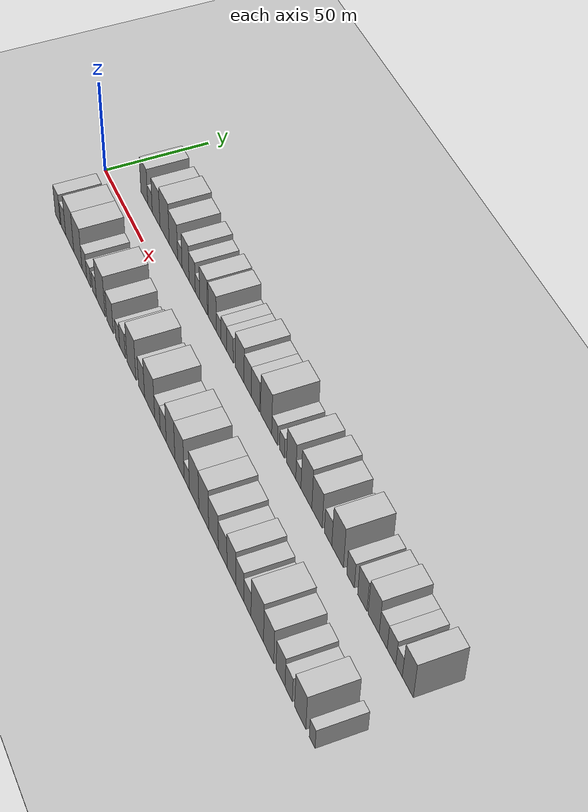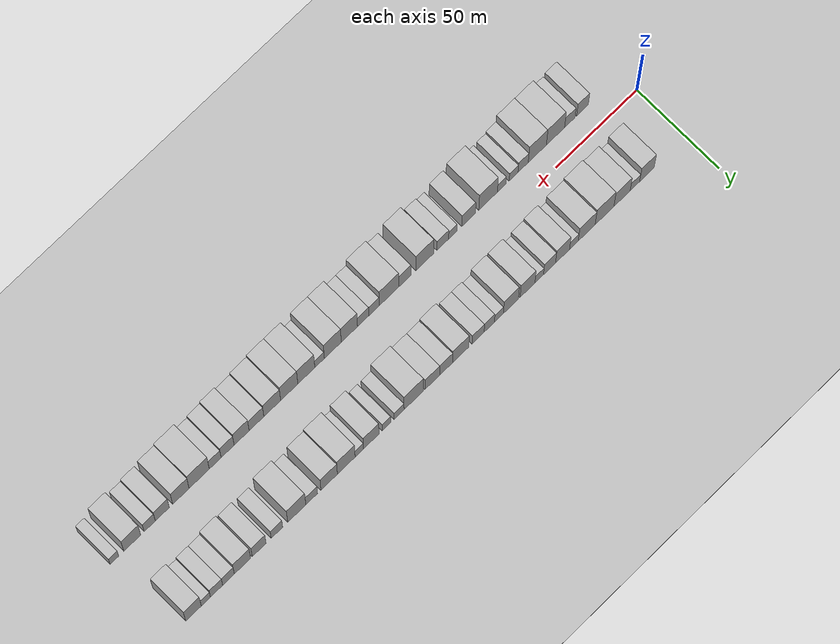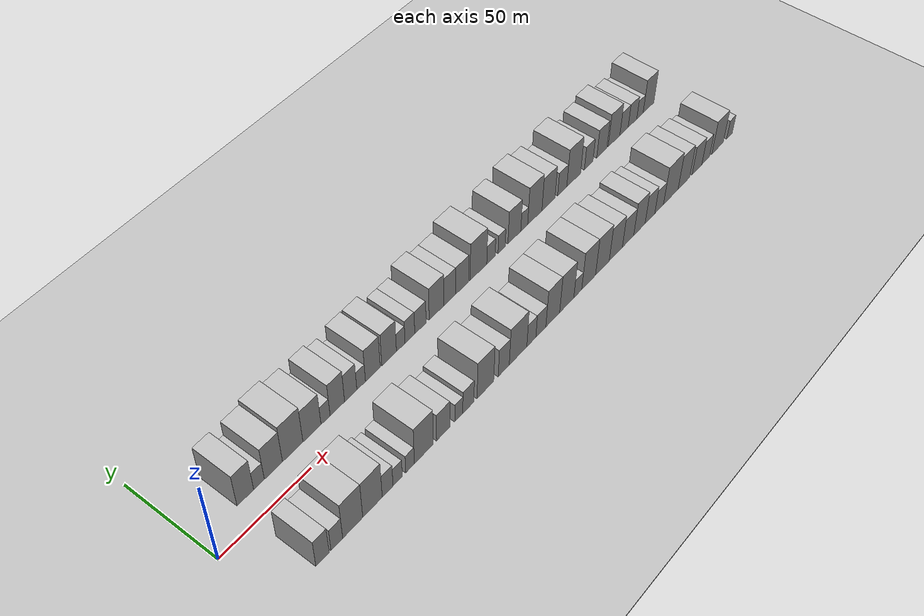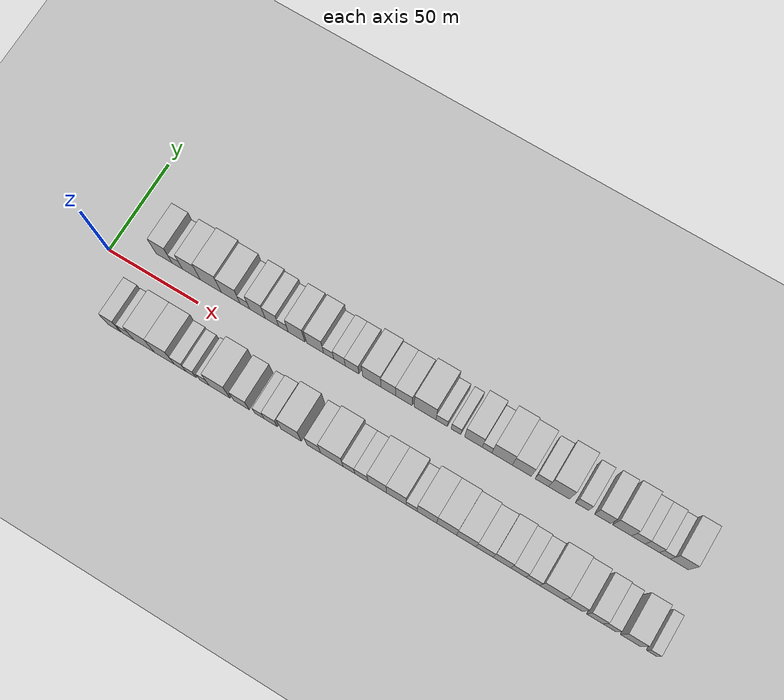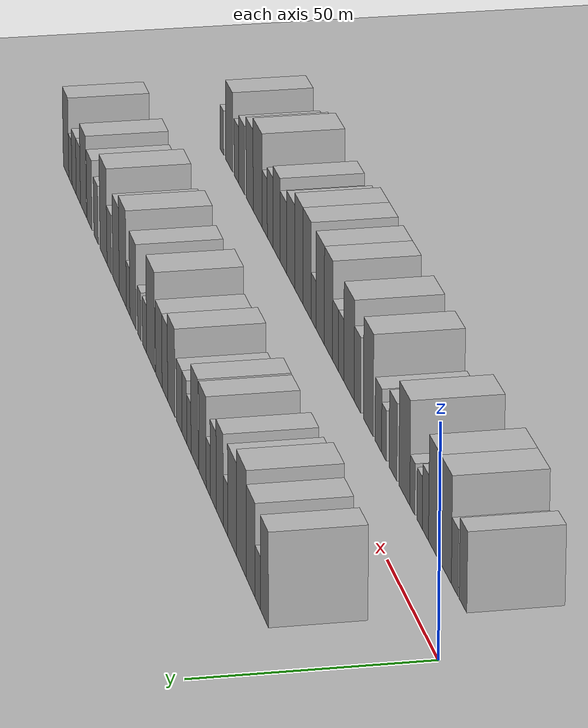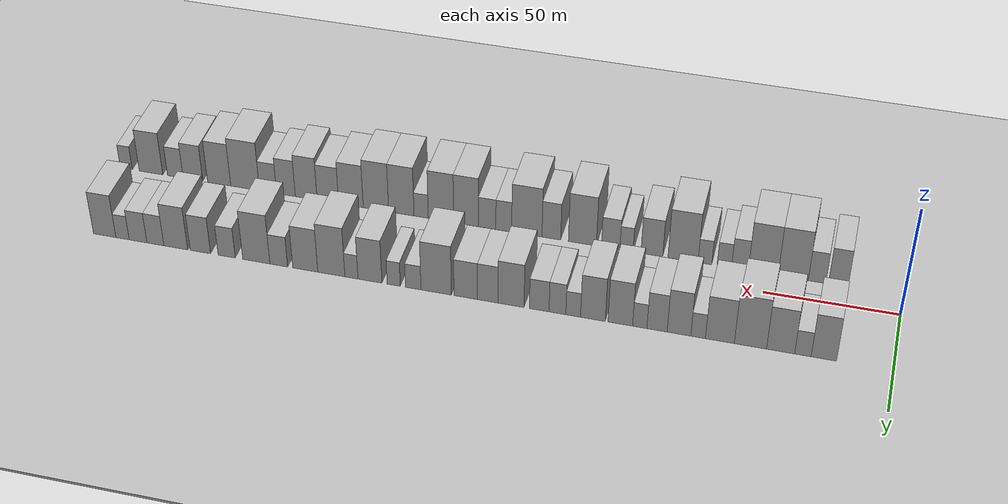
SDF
<?xml version="1.0" encoding="utf-8"?>

<sdf version="1.6">

   <world name="default">

      <gui fullscreen="0">

         <camera name="user_camera">

            <pose>-15 0 4.57585 0 0 0</pose>

            <view_controller>orbit</view_controller>

         </camera>

      </gui>

      <scene>

         <sky>

           <clouds>

             <speed>12</speed>

           </clouds>

         </sky>

         <ambient>0.4 0.4 0.4 1</ambient>

         <background>0.7 0.7 0.7 1</background>

         <shadows>1</shadows>

      </scene>

      <gravity>0 0 -9.8066</gravity>

      <magnetic_field>6e-06 2.3e-05 -4.2e-05</magnetic_field>

      <physics default="0" name="default_physics" type="ode">

         <ode>

            <solver>

               <type>quick</type>

               <iters>10</iters>

               <sor>1.0</sor>

               <use_dynamic_moi_rescaling>0</use_dynamic_moi_rescaling>

            </solver>

            <constraints>

               <cfm>0</cfm>

               <erp>0.2</erp>

               <contact_max_correcting_vel>100</contact_max_correcting_vel>

               <contact_surface_layer>0.001</contact_surface_layer>

            </constraints>

         </ode>

         <max_step_size>0.004</max_step_size>

         <real_time_factor>1</real_time_factor>

         <real_time_update_rate>250</real_time_update_rate>

      </physics>

      <light name="sun" type="directional">

         <cast_shadows>1</cast_shadows>

         <pose>0 0 10 0 0 0</pose>

         <diffuse>0.8 0.8 0.8 1</diffuse>

         <specular>0.2 0.2 0.2 1</specular>

         <attenuation>

            <range>1000</range>

            <constant>0.9</constant>

            <linear>0.01</linear>

            <quadratic>0.001</quadratic>

         </attenuation>

         <direction>-0.5 0.1 -0.9</direction>

      </light>

      <include>

         <name>ground_plane_1</name>

         <uri>model://HANNAS_ground_plane</uri>

         <pose>0 0 0  0 0 0</pose>

      </include>

      <include>

         <name>ground_plane_2</name>

         <uri>model://HANNAS_ground_plane</uri>

         <pose>100 0 0  0 0 0</pose>

      </include>

      <model name="building_1">

         <static>1</static>

         <pose frame="">24.4871 20.0000 0 0.000000 0.000000 1.570796</pose>

         <link name="link">

            <pose frame="">0 0 10.50 0 0 0</pose>

            <collision name="collision">

               <geometry>

                  <box>

                     <size>20.0000 8.9742 21.0000</size>

                  </box>

               </geometry>

               <max_contacts>10</max_contacts>

               <surface>

                  <contact>

                     <ode/>

                  </contact>

                  <bounce/>

                  <friction>

                     <torsional>

                        <ode/>

                     </torsional>

                     <ode/>

                  </friction>

               </surface>

            </collision>

            <visual name="visual">

               <cast_shadows>0</cast_shadows>

               <geometry>

                  <box>

                     <size>20.0000 8.9742 21.0000</size>

                  </box>

               </geometry>

               <material>

                  <script>

                     <uri>model://HANNAS_wall/materials/scripts</uri>

                     <uri>model://HANNAS_wall/materials/textures</uri>

                     <name>vrc/HANNAS_wall</name>

                  </script>

               </material>

            </visual>

            <self_collide>0</self_collide>

            <enable_wind>0</enable_wind>

            <kinematic>0</kinematic>

         </link>

      </model>

      <model name="building_2">

         <static>1</static>

         <pose frame="">31.8893 20.0000 0 0.000000 0.000000 1.570796</pose>

         <link name="link">

            <pose frame="">0 0 6.00 0 0 0</pose>

            <collision name="collision">

               <geometry>

                  <box>

                     <size>20.0000 5.8302 12.0000</size>

                  </box>

               </geometry>

               <max_contacts>10</max_contacts>

               <surface>

                  <contact>

                     <ode/>

                  </contact>

                  <bounce/>

                  <friction>

                     <torsional>

                        <ode/>

                     </torsional>

                     <ode/>

                  </friction>

               </surface>

            </collision>

            <visual name="visual">

               <cast_shadows>0</cast_shadows>

               <geometry>

                  <box>

                     <size>20.0000 5.8302 12.0000</size>

                  </box>

               </geometry>

               <material>

                  <script>

                     <uri>model://HANNAS_wall/materials/scripts</uri>

                     <uri>model://HANNAS_wall/materials/textures</uri>

                     <name>vrc/HANNAS_wall</name>

                  </script>

               </material>

            </visual>

            <self_collide>0</self_collide>

            <enable_wind>0</enable_wind>

            <kinematic>0</kinematic>

         </link>

      </model>

      <model name="building_3">

         <static>1</static>

         <pose frame="">39.8006 20.0000 0 0.000000 0.000000 1.570796</pose>

         <link name="link">

            <pose frame="">0 0 10.50 0 0 0</pose>

            <collision name="collision">

               <geometry>

                  <box>

                     <size>20.0000 9.9923 21.0000</size>

                  </box>

               </geometry>

               <max_contacts>10</max_contacts>

               <surface>

                  <contact>

                     <ode/>

                  </contact>

                  <bounce/>

                  <friction>

                     <torsional>

                        <ode/>

                     </torsional>

                     <ode/>

                  </friction>

               </surface>

            </collision>

            <visual name="visual">

               <cast_shadows>0</cast_shadows>

               <geometry>

                  <box>

                     <size>20.0000 9.9923 21.0000</size>

                  </box>

               </geometry>

               <material>

                  <script>

                     <uri>model://HANNAS_wall/materials/scripts</uri>

                     <uri>model://HANNAS_wall/materials/textures</uri>

                     <name>vrc/HANNAS_wall</name>

                  </script>

               </material>

            </visual>

            <self_collide>0</self_collide>

            <enable_wind>0</enable_wind>

            <kinematic>0</kinematic>

         </link>

      </model>

      <model name="building_4">

         <static>1</static>

         <pose frame="">50.5695 20.0000 0 0.000000 0.000000 1.570796</pose>

         <link name="link">

            <pose frame="">0 0 12.00 0 0 0</pose>

            <collision name="collision">

               <geometry>

                  <box>

                     <size>20.0000 11.5457 24.0000</size>

                  </box>

               </geometry>

               <max_contacts>10</max_contacts>

               <surface>

                  <contact>

                     <ode/>

                  </contact>

                  <bounce/>

                  <friction>

                     <torsional>

                        <ode/>

                     </torsional>

                     <ode/>

                  </friction>

               </surface>

            </collision>

            <visual name="visual">

               <cast_shadows>0</cast_shadows>

               <geometry>

                  <box>

                     <size>20.0000 11.5457 24.0000</size>

                  </box>

               </geometry>

               <material>

                  <script>

                     <uri>model://HANNAS_wall/materials/scripts</uri>

                     <uri>model://HANNAS_wall/materials/textures</uri>

                     <name>vrc/HANNAS_wall</name>

                  </script>

               </material>

            </visual>

            <self_collide>0</self_collide>

            <enable_wind>0</enable_wind>

            <kinematic>0</kinematic>

         </link>

      </model>

      <model name="building_5">

         <static>1</static>

         <pose frame="">61.5440 20.0000 0 0.000000 0.000000 1.570796</pose>

         <link name="link">

            <pose frame="">0 0 10.50 0 0 0</pose>

            <collision name="collision">

               <geometry>

                  <box>

                     <size>20.0000 10.4033 21.0000</size>

                  </box>

               </geometry>

               <max_contacts>10</max_contacts>

               <surface>

                  <contact>

                     <ode/>

                  </contact>

                  <bounce/>

                  <friction>

                     <torsional>

                        <ode/>

                     </torsional>

                     <ode/>

                  </friction>

               </surface>

            </collision>

            <visual name="visual">

               <cast_shadows>0</cast_shadows>

               <geometry>

                  <box>

                     <size>20.0000 10.4033 21.0000</size>

                  </box>

               </geometry>

               <material>

                  <script>

                     <uri>model://HANNAS_wall/materials/scripts</uri>

                     <uri>model://HANNAS_wall/materials/textures</uri>

                     <name>vrc/HANNAS_wall</name>

                  </script>

               </material>

            </visual>

            <self_collide>0</self_collide>

            <enable_wind>0</enable_wind>

            <kinematic>0</kinematic>

         </link>

      </model>

      <model name="building_6">

         <static>1</static>

         <pose frame="">69.3928 20.0000 0 0.000000 0.000000 1.570796</pose>

         <link name="link">

            <pose frame="">0 0 6.00 0 0 0</pose>

            <collision name="collision">

               <geometry>

                  <box>

                     <size>20.0000 5.2942 12.0000</size>

                  </box>

               </geometry>

               <max_contacts>10</max_contacts>

               <surface>

                  <contact>

                     <ode/>

                  </contact>

                  <bounce/>

                  <friction>

                     <torsional>

                        <ode/>

                     </torsional>

                     <ode/>

                  </friction>

               </surface>

            </collision>

            <visual name="visual">

               <cast_shadows>0</cast_shadows>

               <geometry>

                  <box>

                     <size>20.0000 5.2942 12.0000</size>

                  </box>

               </geometry>

               <material>

                  <script>

                     <uri>model://HANNAS_wall/materials/scripts</uri>

                     <uri>model://HANNAS_wall/materials/textures</uri>

                     <name>vrc/HANNAS_wall</name>

                  </script>

               </material>

            </visual>

            <self_collide>0</self_collide>

            <enable_wind>0</enable_wind>

            <kinematic>0</kinematic>

         </link>

      </model>

      <model name="building_7">

         <static>1</static>

         <pose frame="">76.3255 20.0000 0 0.000000 0.000000 1.570796</pose>

         <link name="link">

            <pose frame="">0 0 10.50 0 0 0</pose>

            <collision name="collision">

               <geometry>

                  <box>

                     <size>20.0000 8.5712 21.0000</size>

                  </box>

               </geometry>

               <max_contacts>10</max_contacts>

               <surface>

                  <contact>

                     <ode/>

                  </contact>

                  <bounce/>

                  <friction>

                     <torsional>

                        <ode/>

                     </torsional>

                     <ode/>

                  </friction>

               </surface>

            </collision>

            <visual name="visual">

               <cast_shadows>0</cast_shadows>

               <geometry>

                  <box>

                     <size>20.0000 8.5712 21.0000</size>

                  </box>

               </geometry>

               <material>

                  <script>

                     <uri>model://HANNAS_wall/materials/scripts</uri>

                     <uri>model://HANNAS_wall/materials/textures</uri>

                     <name>vrc/HANNAS_wall</name>

                  </script>

               </material>

            </visual>

            <self_collide>0</self_collide>

            <enable_wind>0</enable_wind>

            <kinematic>0</kinematic>

         </link>

      </model>

      <model name="building_8">

         <static>1</static>

         <pose frame="">84.2975 20.0000 0 0.000000 0.000000 1.570796</pose>

         <link name="link">

            <pose frame="">0 0 9.00 0 0 0</pose>

            <collision name="collision">

               <geometry>

                  <box>

                     <size>20.0000 7.3727 18.0000</size>

                  </box>

               </geometry>

               <max_contacts>10</max_contacts>

               <surface>

                  <contact>

                     <ode/>

                  </contact>

                  <bounce/>

                  <friction>

                     <torsional>

                        <ode/>

                     </torsional>

                     <ode/>

                  </friction>

               </surface>

            </collision>

            <visual name="visual">

               <cast_shadows>0</cast_shadows>

               <geometry>

                  <box>

                     <size>20.0000 7.3727 18.0000</size>

                  </box>

               </geometry>

               <material>

                  <script>

                     <uri>model://HANNAS_wall/materials/scripts</uri>

                     <uri>model://HANNAS_wall/materials/textures</uri>

                     <name>vrc/HANNAS_wall</name>

                  </script>

               </material>

            </visual>

            <self_collide>0</self_collide>

            <enable_wind>0</enable_wind>

            <kinematic>0</kinematic>

         </link>

      </model>

      <model name="building_9">

         <static>1</static>

         <pose frame="">90.5902 20.0000 0 0.000000 0.000000 1.570796</pose>

         <link name="link">

            <pose frame="">0 0 6.00 0 0 0</pose>

            <collision name="collision">

               <geometry>

                  <box>

                     <size>20.0000 5.2127 12.0000</size>

                  </box>

               </geometry>

               <max_contacts>10</max_contacts>

               <surface>

                  <contact>

                     <ode/>

                  </contact>

                  <bounce/>

                  <friction>

                     <torsional>

                        <ode/>

                     </torsional>

                     <ode/>

                  </friction>

               </surface>

            </collision>

            <visual name="visual">

               <cast_shadows>0</cast_shadows>

               <geometry>

                  <box>

                     <size>20.0000 5.2127 12.0000</size>

                  </box>

               </geometry>

               <material>

                  <script>

                     <uri>model://HANNAS_wall/materials/scripts</uri>

                     <uri>model://HANNAS_wall/materials/textures</uri>

                     <name>vrc/HANNAS_wall</name>

                  </script>

               </material>

            </visual>

            <self_collide>0</self_collide>

            <enable_wind>0</enable_wind>

            <kinematic>0</kinematic>

         </link>

      </model>

      <model name="building_10">

         <static>1</static>

         <pose frame="">97.7209 20.0000 0 0.000000 0.000000 1.570796</pose>

         <link name="link">

            <pose frame="">0 0 10.50 0 0 0</pose>

            <collision name="collision">

               <geometry>

                  <box>

                     <size>20.0000 9.0488 21.0000</size>

                  </box>

               </geometry>

               <max_contacts>10</max_contacts>

               <surface>

                  <contact>

                     <ode/>

                  </contact>

                  <bounce/>

                  <friction>

                     <torsional>

                        <ode/>

                     </torsional>

                     <ode/>

                  </friction>

               </surface>

            </collision>

            <visual name="visual">

               <cast_shadows>0</cast_shadows>

               <geometry>

                  <box>

                     <size>20.0000 9.0488 21.0000</size>

                  </box>

               </geometry>

               <material>

                  <script>

                     <uri>model://HANNAS_wall/materials/scripts</uri>

                     <uri>model://HANNAS_wall/materials/textures</uri>

                     <name>vrc/HANNAS_wall</name>

                  </script>

               </material>

            </visual>

            <self_collide>0</self_collide>

            <enable_wind>0</enable_wind>

            <kinematic>0</kinematic>

         </link>

      </model>

      <model name="building_11">

         <static>1</static>

         <pose frame="">107.8234 20.0000 0 0.000000 0.000000 1.570796</pose>

         <link name="link">

            <pose frame="">0 0 10.50 0 0 0</pose>

            <collision name="collision">

               <geometry>

                  <box>

                     <size>20.0000 9.1562 21.0000</size>

                  </box>

               </geometry>

               <max_contacts>10</max_contacts>

               <surface>

                  <contact>

                     <ode/>

                  </contact>

                  <bounce/>

                  <friction>

                     <torsional>

                        <ode/>

                     </torsional>

                     <ode/>

                  </friction>

               </surface>

            </collision>

            <visual name="visual">

               <cast_shadows>0</cast_shadows>

               <geometry>

                  <box>

                     <size>20.0000 9.1562 21.0000</size>

                  </box>

               </geometry>

               <material>

                  <script>

                     <uri>model://HANNAS_wall/materials/scripts</uri>

                     <uri>model://HANNAS_wall/materials/textures</uri>

                     <name>vrc/HANNAS_wall</name>

                  </script>

               </material>

            </visual>

            <self_collide>0</self_collide>

            <enable_wind>0</enable_wind>

            <kinematic>0</kinematic>

         </link>

      </model>

      <model name="building_12">

         <static>1</static>

         <pose frame="">115.1176 20.0000 0 0.000000 0.000000 1.570796</pose>

         <link name="link">

            <pose frame="">0 0 6.00 0 0 0</pose>

            <collision name="collision">

               <geometry>

                  <box>

                     <size>20.0000 5.4322 12.0000</size>

                  </box>

               </geometry>

               <max_contacts>10</max_contacts>

               <surface>

                  <contact>

                     <ode/>

                  </contact>

                  <bounce/>

                  <friction>

                     <torsional>

                        <ode/>

                     </torsional>

                     <ode/>

                  </friction>

               </surface>

            </collision>

            <visual name="visual">

               <cast_shadows>0</cast_shadows>

               <geometry>

                  <box>

                     <size>20.0000 5.4322 12.0000</size>

                  </box>

               </geometry>

               <material>

                  <script>

                     <uri>model://HANNAS_wall/materials/scripts</uri>

                     <uri>model://HANNAS_wall/materials/textures</uri>

                     <name>vrc/HANNAS_wall</name>

                  </script>

               </material>

            </visual>

            <self_collide>0</self_collide>

            <enable_wind>0</enable_wind>

            <kinematic>0</kinematic>

         </link>

      </model>

      <model name="building_13">

         <static>1</static>

         <pose frame="">120.9533 20.0000 0 0.000000 0.000000 1.570796</pose>

         <link name="link">

            <pose frame="">0 0 7.50 0 0 0</pose>

            <collision name="collision">

               <geometry>

                  <box>

                     <size>20.0000 6.2392 15.0000</size>

                  </box>

               </geometry>

               <max_contacts>10</max_contacts>

               <surface>

                  <contact>

                     <ode/>

                  </contact>

                  <bounce/>

                  <friction>

                     <torsional>

                        <ode/>

                     </torsional>

                     <ode/>

                  </friction>

               </surface>

            </collision>

            <visual name="visual">

               <cast_shadows>0</cast_shadows>

               <geometry>

                  <box>

                     <size>20.0000 6.2392 15.0000</size>

                  </box>

               </geometry>

               <material>

                  <script>

                     <uri>model://HANNAS_wall/materials/scripts</uri>

                     <uri>model://HANNAS_wall/materials/textures</uri>

                     <name>vrc/HANNAS_wall</name>

                  </script>

               </material>

            </visual>

            <self_collide>0</self_collide>

            <enable_wind>0</enable_wind>

            <kinematic>0</kinematic>

         </link>

      </model>

      <model name="building_14">

         <static>1</static>

         <pose frame="">127.7393 20.0000 0 0.000000 0.000000 1.570796</pose>

         <link name="link">

            <pose frame="">0 0 7.50 0 0 0</pose>

            <collision name="collision">

               <geometry>

                  <box>

                     <size>20.0000 7.3328 15.0000</size>

                  </box>

               </geometry>

               <max_contacts>10</max_contacts>

               <surface>

                  <contact>

                     <ode/>

                  </contact>

                  <bounce/>

                  <friction>

                     <torsional>

                        <ode/>

                     </torsional>

                     <ode/>

                  </friction>

               </surface>

            </collision>

            <visual name="visual">

               <cast_shadows>0</cast_shadows>

               <geometry>

                  <box>

                     <size>20.0000 7.3328 15.0000</size>

                  </box>

               </geometry>

               <material>

                  <script>

                     <uri>model://HANNAS_wall/materials/scripts</uri>

                     <uri>model://HANNAS_wall/materials/textures</uri>

                     <name>vrc/HANNAS_wall</name>

                  </script>

               </material>

            </visual>

            <self_collide>0</self_collide>

            <enable_wind>0</enable_wind>

            <kinematic>0</kinematic>

         </link>

      </model>

      <model name="building_15">

         <static>1</static>

         <pose frame="">138.3168 20.0000 0 0.000000 0.000000 1.570796</pose>

         <link name="link">

            <pose frame="">0 0 10.50 0 0 0</pose>

            <collision name="collision">

               <geometry>

                  <box>

                     <size>20.0000 9.8221 21.0000</size>

                  </box>

               </geometry>

               <max_contacts>10</max_contacts>

               <surface>

                  <contact>

                     <ode/>

                  </contact>

                  <bounce/>

                  <friction>

                     <torsional>

                        <ode/>

                     </torsional>

                     <ode/>

                  </friction>

               </surface>

            </collision>

            <visual name="visual">

               <cast_shadows>0</cast_shadows>

               <geometry>

                  <box>

                     <size>20.0000 9.8221 21.0000</size>

                  </box>

               </geometry>

               <material>

                  <script>

                     <uri>model://HANNAS_wall/materials/scripts</uri>

                     <uri>model://HANNAS_wall/materials/textures</uri>

                     <name>vrc/HANNAS_wall</name>

                  </script>

               </material>

            </visual>

            <self_collide>0</self_collide>

            <enable_wind>0</enable_wind>

            <kinematic>0</kinematic>

         </link>

      </model>

      <model name="building_16">

         <static>1</static>

         <pose frame="">147.0808 20.0000 0 0.000000 0.000000 1.570796</pose>

         <link name="link">

            <pose frame="">0 0 9.00 0 0 0</pose>

            <collision name="collision">

               <geometry>

                  <box>

                     <size>20.0000 7.7059 18.0000</size>

                  </box>

               </geometry>

               <max_contacts>10</max_contacts>

               <surface>

                  <contact>

                     <ode/>

                  </contact>

                  <bounce/>

                  <friction>

                     <torsional>

                        <ode/>

                     </torsional>

                     <ode/>

                  </friction>

               </surface>

            </collision>

            <visual name="visual">

               <cast_shadows>0</cast_shadows>

               <geometry>

                  <box>

                     <size>20.0000 7.7059 18.0000</size>

                  </box>

               </geometry>

               <material>

                  <script>

                     <uri>model://HANNAS_wall/materials/scripts</uri>

                     <uri>model://HANNAS_wall/materials/textures</uri>

                     <name>vrc/HANNAS_wall</name>

                  </script>

               </material>

            </visual>

            <self_collide>0</self_collide>

            <enable_wind>0</enable_wind>

            <kinematic>0</kinematic>

         </link>

      </model>

      <model name="building_17">

         <static>1</static>

         <pose frame="">155.3812 20.0000 0 0.000000 0.000000 1.570796</pose>

         <link name="link">

            <pose frame="">0 0 9.00 0 0 0</pose>

            <collision name="collision">

               <geometry>

                  <box>

                     <size>20.0000 8.8951 18.0000</size>

                  </box>

               </geometry>

               <max_contacts>10</max_contacts>

               <surface>

                  <contact>

                     <ode/>

                  </contact>

                  <bounce/>

                  <friction>

                     <torsional>

                        <ode/>

                     </torsional>

                     <ode/>

                  </friction>

               </surface>

            </collision>

            <visual name="visual">

               <cast_shadows>0</cast_shadows>

               <geometry>

                  <box>

                     <size>20.0000 8.8951 18.0000</size>

                  </box>

               </geometry>

               <material>

                  <script>

                     <uri>model://HANNAS_wall/materials/scripts</uri>

                     <uri>model://HANNAS_wall/materials/textures</uri>

                     <name>vrc/HANNAS_wall</name>

                  </script>

               </material>

            </visual>

            <self_collide>0</self_collide>

            <enable_wind>0</enable_wind>

            <kinematic>0</kinematic>

         </link>

      </model>

      <model name="building_18">

         <static>1</static>

         <pose frame="">166.6293 20.0000 0 0.000000 0.000000 1.570796</pose>

         <link name="link">

            <pose frame="">0 0 12.00 0 0 0</pose>

            <collision name="collision">

               <geometry>

                  <box>

                     <size>20.0000 11.6011 24.0000</size>

                  </box>

               </geometry>

               <max_contacts>10</max_contacts>

               <surface>

                  <contact>

                     <ode/>

                  </contact>

                  <bounce/>

                  <friction>

                     <torsional>

                        <ode/>

                     </torsional>

                     <ode/>

                  </friction>

               </surface>

            </collision>

            <visual name="visual">

               <cast_shadows>0</cast_shadows>

               <geometry>

                  <box>

                     <size>20.0000 11.6011 24.0000</size>

                  </box>

               </geometry>

               <material>

                  <script>

                     <uri>model://HANNAS_wall/materials/scripts</uri>

                     <uri>model://HANNAS_wall/materials/textures</uri>

                     <name>vrc/HANNAS_wall</name>

                  </script>

               </material>

            </visual>

            <self_collide>0</self_collide>

            <enable_wind>0</enable_wind>

            <kinematic>0</kinematic>

         </link>

      </model>

      <model name="building_19">

         <static>1</static>

         <pose frame="">175.3966 20.0000 0 0.000000 0.000000 1.570796</pose>

         <link name="link">

            <pose frame="">0 0 6.00 0 0 0</pose>

            <collision name="collision">

               <geometry>

                  <box>

                     <size>20.0000 5.9334 12.0000</size>

                  </box>

               </geometry>

               <max_contacts>10</max_contacts>

               <surface>

                  <contact>

                     <ode/>

                  </contact>

                  <bounce/>

                  <friction>

                     <torsional>

                        <ode/>

                     </torsional>

                     <ode/>

                  </friction>

               </surface>

            </collision>

            <visual name="visual">

               <cast_shadows>0</cast_shadows>

               <geometry>

                  <box>

                     <size>20.0000 5.9334 12.0000</size>

                  </box>

               </geometry>

               <material>

                  <script>

                     <uri>model://HANNAS_wall/materials/scripts</uri>

                     <uri>model://HANNAS_wall/materials/textures</uri>

                     <name>vrc/HANNAS_wall</name>

                  </script>

               </material>

            </visual>

            <self_collide>0</self_collide>

            <enable_wind>0</enable_wind>

            <kinematic>0</kinematic>

         </link>

      </model>

      <model name="building_20">

         <static>1</static>

         <pose frame="">182.8956 20.0000 0 0.000000 0.000000 1.570796</pose>

         <link name="link">

            <pose frame="">0 0 6.00 0 0 0</pose>

            <collision name="collision">

               <geometry>

                  <box>

                     <size>20.0000 5.0646 12.0000</size>

                  </box>

               </geometry>

               <max_contacts>10</max_contacts>

               <surface>

                  <contact>

                     <ode/>

                  </contact>

                  <bounce/>

                  <friction>

                     <torsional>

                        <ode/>

                     </torsional>

                     <ode/>

                  </friction>

               </surface>

            </collision>

            <visual name="visual">

               <cast_shadows>0</cast_shadows>

               <geometry>

                  <box>

                     <size>20.0000 5.0646 12.0000</size>

                  </box>

               </geometry>

               <material>

                  <script>

                     <uri>model://HANNAS_wall/materials/scripts</uri>

                     <uri>model://HANNAS_wall/materials/textures</uri>

                     <name>vrc/HANNAS_wall</name>

                  </script>

               </material>

            </visual>

            <self_collide>0</self_collide>

            <enable_wind>0</enable_wind>

            <kinematic>0</kinematic>

         </link>

      </model>

      <model name="building_21">

         <static>1</static>

         <pose frame="">192.0635 20.0000 0 0.000000 0.000000 1.570796</pose>

         <link name="link">

            <pose frame="">0 0 10.50 0 0 0</pose>

            <collision name="collision">

               <geometry>

                  <box>

                     <size>20.0000 9.2713 21.0000</size>

                  </box>

               </geometry>

               <max_contacts>10</max_contacts>

               <surface>

                  <contact>

                     <ode/>

                  </contact>

                  <bounce/>

                  <friction>

                     <torsional>

                        <ode/>

                     </torsional>

                     <ode/>

                  </friction>

               </surface>

            </collision>

            <visual name="visual">

               <cast_shadows>0</cast_shadows>

               <geometry>

                  <box>

                     <size>20.0000 9.2713 21.0000</size>

                  </box>

               </geometry>

               <material>

                  <script>

                     <uri>model://HANNAS_wall/materials/scripts</uri>

                     <uri>model://HANNAS_wall/materials/textures</uri>

                     <name>vrc/HANNAS_wall</name>

                  </script>

               </material>

            </visual>

            <self_collide>0</self_collide>

            <enable_wind>0</enable_wind>

            <kinematic>0</kinematic>

         </link>

      </model>

      <model name="building_22">

         <static>1</static>

         <pose frame="">199.2287 20.0000 0 0.000000 0.000000 1.570796</pose>

         <link name="link">

            <pose frame="">0 0 6.00 0 0 0</pose>

            <collision name="collision">

               <geometry>

                  <box>

                     <size>20.0000 5.0590 12.0000</size>

                  </box>

               </geometry>

               <max_contacts>10</max_contacts>

               <surface>

                  <contact>

                     <ode/>

                  </contact>

                  <bounce/>

                  <friction>

                     <torsional>

                        <ode/>

                     </torsional>

                     <ode/>

                  </friction>

               </surface>

            </collision>

            <visual name="visual">

               <cast_shadows>0</cast_shadows>

               <geometry>

                  <box>

                     <size>20.0000 5.0590 12.0000</size>

                  </box>

               </geometry>

               <material>

                  <script>

                     <uri>model://HANNAS_wall/materials/scripts</uri>

                     <uri>model://HANNAS_wall/materials/textures</uri>

                     <name>vrc/HANNAS_wall</name>

                  </script>

               </material>

            </visual>

            <self_collide>0</self_collide>

            <enable_wind>0</enable_wind>

            <kinematic>0</kinematic>

         </link>

      </model>

      <model name="building_23">

         <static>1</static>

         <pose frame="">207.0410 20.0000 0 0.000000 0.000000 1.570796</pose>

         <link name="link">

            <pose frame="">0 0 12.00 0 0 0</pose>

            <collision name="collision">

               <geometry>

                  <box>

                     <size>20.0000 10.5656 24.0000</size>

                  </box>

               </geometry>

               <max_contacts>10</max_contacts>

               <surface>

                  <contact>

                     <ode/>

                  </contact>

                  <bounce/>

                  <friction>

                     <torsional>

                        <ode/>

                     </torsional>

                     <ode/>

                  </friction>

               </surface>

            </collision>

            <visual name="visual">

               <cast_shadows>0</cast_shadows>

               <geometry>

                  <box>

                     <size>20.0000 10.5656 24.0000</size>

                  </box>

               </geometry>

               <material>

                  <script>

                     <uri>model://HANNAS_wall/materials/scripts</uri>

                     <uri>model://HANNAS_wall/materials/textures</uri>

                     <name>vrc/HANNAS_wall</name>

                  </script>

               </material>

            </visual>

            <self_collide>0</self_collide>

            <enable_wind>0</enable_wind>

            <kinematic>0</kinematic>

         </link>

      </model>

      <model name="building_24">

         <static>1</static>

         <pose frame="">217.2430 20.0000 0 0.000000 0.000000 1.570796</pose>

         <link name="link">

            <pose frame="">0 0 10.50 0 0 0</pose>

            <collision name="collision">

               <geometry>

                  <box>

                     <size>20.0000 9.8382 21.0000</size>

                  </box>

               </geometry>

               <max_contacts>10</max_contacts>

               <surface>

                  <contact>

                     <ode/>

                  </contact>

                  <bounce/>

                  <friction>

                     <torsional>

                        <ode/>

                     </torsional>

                     <ode/>

                  </friction>

               </surface>

            </collision>

            <visual name="visual">

               <cast_shadows>0</cast_shadows>

               <geometry>

                  <box>

                     <size>20.0000 9.8382 21.0000</size>

                  </box>

               </geometry>

               <material>

                  <script>

                     <uri>model://HANNAS_wall/materials/scripts</uri>

                     <uri>model://HANNAS_wall/materials/textures</uri>

                     <name>vrc/HANNAS_wall</name>

                  </script>

               </material>

            </visual>

            <self_collide>0</self_collide>

            <enable_wind>0</enable_wind>

            <kinematic>0</kinematic>

         </link>

      </model>

      <model name="building_25">

         <static>1</static>

         <pose frame="">227.6580 20.0000 0 0.000000 0.000000 1.570796</pose>

         <link name="link">

            <pose frame="">0 0 7.50 0 0 0</pose>

            <collision name="collision">

               <geometry>

                  <box>

                     <size>20.0000 6.9918 15.0000</size>

                  </box>

               </geometry>

               <max_contacts>10</max_contacts>

               <surface>

                  <contact>

                     <ode/>

                  </contact>

                  <bounce/>

                  <friction>

                     <torsional>

                        <ode/>

                     </torsional>

                     <ode/>

                  </friction>

               </surface>

            </collision>

            <visual name="visual">

               <cast_shadows>0</cast_shadows>

               <geometry>

                  <box>

                     <size>20.0000 6.9918 15.0000</size>

                  </box>

               </geometry>

               <material>

                  <script>

                     <uri>model://HANNAS_wall/materials/scripts</uri>

                     <uri>model://HANNAS_wall/materials/textures</uri>

                     <name>vrc/HANNAS_wall</name>

                  </script>

               </material>

            </visual>

            <self_collide>0</self_collide>

            <enable_wind>0</enable_wind>

            <kinematic>0</kinematic>

         </link>

      </model>

      <model name="building_26">

         <static>1</static>

         <pose frame="">236.5223 20.0000 0 0.000000 0.000000 1.570796</pose>

         <link name="link">

            <pose frame="">0 0 12.00 0 0 0</pose>

            <collision name="collision">

               <geometry>

                  <box>

                     <size>20.0000 10.7368 24.0000</size>

                  </box>

               </geometry>

               <max_contacts>10</max_contacts>

               <surface>

                  <contact>

                     <ode/>

                  </contact>

                  <bounce/>

                  <friction>

                     <torsional>

                        <ode/>

                     </torsional>

                     <ode/>

                  </friction>

               </surface>

            </collision>

            <visual name="visual">

               <cast_shadows>0</cast_shadows>

               <geometry>

                  <box>

                     <size>20.0000 10.7368 24.0000</size>

                  </box>

               </geometry>

               <material>

                  <script>

                     <uri>model://HANNAS_wall/materials/scripts</uri>

                     <uri>model://HANNAS_wall/materials/textures</uri>

                     <name>vrc/HANNAS_wall</name>

                  </script>

               </material>

            </visual>

            <self_collide>0</self_collide>

            <enable_wind>0</enable_wind>

            <kinematic>0</kinematic>

         </link>

      </model>

      <model name="building_27">

         <static>1</static>

         <pose frame="">248.2994 20.0000 0 0.000000 0.000000 1.570796</pose>

         <link name="link">

            <pose frame="">0 0 7.50 0 0 0</pose>

            <collision name="collision">

               <geometry>

                  <box>

                     <size>20.0000 6.8175 15.0000</size>

                  </box>

               </geometry>

               <max_contacts>10</max_contacts>

               <surface>

                  <contact>

                     <ode/>

                  </contact>

                  <bounce/>

                  <friction>

                     <torsional>

                        <ode/>

                     </torsional>

                     <ode/>

                  </friction>

               </surface>

            </collision>

            <visual name="visual">

               <cast_shadows>0</cast_shadows>

               <geometry>

                  <box>

                     <size>20.0000 6.8175 15.0000</size>

                  </box>

               </geometry>

               <material>

                  <script>

                     <uri>model://HANNAS_wall/materials/scripts</uri>

                     <uri>model://HANNAS_wall/materials/textures</uri>

                     <name>vrc/HANNAS_wall</name>

                  </script>

               </material>

            </visual>

            <self_collide>0</self_collide>

            <enable_wind>0</enable_wind>

            <kinematic>0</kinematic>

         </link>

      </model>

      <model name="building_28">

         <static>1</static>

         <pose frame="">258.8060 20.0000 0 0.000000 0.000000 1.570796</pose>

         <link name="link">

            <pose frame="">0 0 9.00 0 0 0</pose>

            <collision name="collision">

               <geometry>

                  <box>

                     <size>20.0000 8.1957 18.0000</size>

                  </box>

               </geometry>

               <max_contacts>10</max_contacts>

               <surface>

                  <contact>

                     <ode/>

                  </contact>

                  <bounce/>

                  <friction>

                     <torsional>

                        <ode/>

                     </torsional>

                     <ode/>

                  </friction>

               </surface>

            </collision>

            <visual name="visual">

               <cast_shadows>0</cast_shadows>

               <geometry>

                  <box>

                     <size>20.0000 8.1957 18.0000</size>

                  </box>

               </geometry>

               <material>

                  <script>

                     <uri>model://HANNAS_wall/materials/scripts</uri>

                     <uri>model://HANNAS_wall/materials/textures</uri>

                     <name>vrc/HANNAS_wall</name>

                  </script>

               </material>

            </visual>

            <self_collide>0</self_collide>

            <enable_wind>0</enable_wind>

            <kinematic>0</kinematic>

         </link>

      </model>

      <model name="building_29">

         <static>1</static>

         <pose frame="">268.7011 20.0000 0 0.000000 0.000000 1.570796</pose>

         <link name="link">

            <pose frame="">0 0 10.50 0 0 0</pose>

            <collision name="collision">

               <geometry>

                  <box>

                     <size>20.0000 9.5946 21.0000</size>

                  </box>

               </geometry>

               <max_contacts>10</max_contacts>

               <surface>

                  <contact>

                     <ode/>

                  </contact>

                  <bounce/>

                  <friction>

                     <torsional>

                        <ode/>

                     </torsional>

                     <ode/>

                  </friction>

               </surface>

            </collision>

            <visual name="visual">

               <cast_shadows>0</cast_shadows>

               <geometry>

                  <box>

                     <size>20.0000 9.5946 21.0000</size>

                  </box>

               </geometry>

               <material>

                  <script>

                     <uri>model://HANNAS_wall/materials/scripts</uri>

                     <uri>model://HANNAS_wall/materials/textures</uri>

                     <name>vrc/HANNAS_wall</name>

                  </script>

               </material>

            </visual>

            <self_collide>0</self_collide>

            <enable_wind>0</enable_wind>

            <kinematic>0</kinematic>

         </link>

      </model>

      <model name="building_30">

         <static>1</static>

         <pose frame="">276.9308 20.0000 0 0.000000 0.000000 1.570796</pose>

         <link name="link">

            <pose frame="">0 0 7.50 0 0 0</pose>

            <collision name="collision">

               <geometry>

                  <box>

                     <size>20.0000 6.8648 15.0000</size>

                  </box>

               </geometry>

               <max_contacts>10</max_contacts>

               <surface>

                  <contact>

                     <ode/>

                  </contact>

                  <bounce/>

                  <friction>

                     <torsional>

                        <ode/>

                     </torsional>

                     <ode/>

                  </friction>

               </surface>

            </collision>

            <visual name="visual">

               <cast_shadows>0</cast_shadows>

               <geometry>

                  <box>

                     <size>20.0000 6.8648 15.0000</size>

                  </box>

               </geometry>

               <material>

                  <script>

                     <uri>model://HANNAS_wall/materials/scripts</uri>

                     <uri>model://HANNAS_wall/materials/textures</uri>

                     <name>vrc/HANNAS_wall</name>

                  </script>

               </material>

            </visual>

            <self_collide>0</self_collide>

            <enable_wind>0</enable_wind>

            <kinematic>0</kinematic>

         </link>

      </model>

      <model name="building_31">

         <static>1</static>

         <pose frame="">283.9594 20.0000 0 0.000000 0.000000 1.570796</pose>

         <link name="link">

            <pose frame="">0 0 7.50 0 0 0</pose>

            <collision name="collision">

               <geometry>

                  <box>

                     <size>20.0000 7.1924 15.0000</size>

                  </box>

               </geometry>

               <max_contacts>10</max_contacts>

               <surface>

                  <contact>

                     <ode/>

                  </contact>

                  <bounce/>

                  <friction>

                     <torsional>

                        <ode/>

                     </torsional>

                     <ode/>

                  </friction>

               </surface>

            </collision>

            <visual name="visual">

               <cast_shadows>0</cast_shadows>

               <geometry>

                  <box>

                     <size>20.0000 7.1924 15.0000</size>

                  </box>

               </geometry>

               <material>

                  <script>

                     <uri>model://HANNAS_wall/materials/scripts</uri>

                     <uri>model://HANNAS_wall/materials/textures</uri>

                     <name>vrc/HANNAS_wall</name>

                  </script>

               </material>

            </visual>

            <self_collide>0</self_collide>

            <enable_wind>0</enable_wind>

            <kinematic>0</kinematic>

         </link>

      </model>

      <model name="building_32">

         <static>1</static>

         <pose frame="">290.2627 20.0000 0 0.000000 0.000000 1.570796</pose>

         <link name="link">

            <pose frame="">0 0 6.00 0 0 0</pose>

            <collision name="collision">

               <geometry>

                  <box>

                     <size>20.0000 5.4142 12.0000</size>

                  </box>

               </geometry>

               <max_contacts>10</max_contacts>

               <surface>

                  <contact>

                     <ode/>

                  </contact>

                  <bounce/>

                  <friction>

                     <torsional>

                        <ode/>

                     </torsional>

                     <ode/>

                  </friction>

               </surface>

            </collision>

            <visual name="visual">

               <cast_shadows>0</cast_shadows>

               <geometry>

                  <box>

                     <size>20.0000 5.4142 12.0000</size>

                  </box>

               </geometry>

               <material>

                  <script>

                     <uri>model://HANNAS_wall/materials/scripts</uri>

                     <uri>model://HANNAS_wall/materials/textures</uri>

                     <name>vrc/HANNAS_wall</name>

                  </script>

               </material>

            </visual>

            <self_collide>0</self_collide>

            <enable_wind>0</enable_wind>

            <kinematic>0</kinematic>

         </link>

      </model>

      <model name="building_33">

         <static>1</static>

         <pose frame="">297.5388 20.0000 0 0.000000 0.000000 1.570796</pose>

         <link name="link">

            <pose frame="">0 0 10.50 0 0 0</pose>

            <collision name="collision">

               <geometry>

                  <box>

                     <size>20.0000 9.1381 21.0000</size>

                  </box>

               </geometry>

               <max_contacts>10</max_contacts>

               <surface>

                  <contact>

                     <ode/>

                  </contact>

                  <bounce/>

                  <friction>

                     <torsional>

                        <ode/>

                     </torsional>

                     <ode/>

                  </friction>

               </surface>

            </collision>

            <visual name="visual">

               <cast_shadows>0</cast_shadows>

               <geometry>

                  <box>

                     <size>20.0000 9.1381 21.0000</size>

                  </box>

               </geometry>

               <material>

                  <script>

                     <uri>model://HANNAS_wall/materials/scripts</uri>

                     <uri>model://HANNAS_wall/materials/textures</uri>

                     <name>vrc/HANNAS_wall</name>

                  </script>

               </material>

            </visual>

            <self_collide>0</self_collide>

            <enable_wind>0</enable_wind>

            <kinematic>0</kinematic>

         </link>

      </model>

      <model name="building_34">

         <static>1</static>

         <pose frame="">23.6063 -20.0000 0 0.000000 0.000000 1.570796</pose>

         <link name="link">

            <pose frame="">0 0 9.00 0 0 0</pose>

            <collision name="collision">

               <geometry>

                  <box>

                     <size>20.0000 7.2125 18.0000</size>

                  </box>

               </geometry>

               <max_contacts>10</max_contacts>

               <surface>

                  <contact>

                     <ode/>

                  </contact>

                  <bounce/>

                  <friction>

                     <torsional>

                        <ode/>

                     </torsional>

                     <ode/>

                  </friction>

               </surface>

            </collision>

            <visual name="visual">

               <cast_shadows>0</cast_shadows>

               <geometry>

                  <box>

                     <size>20.0000 7.2125 18.0000</size>

                  </box>

               </geometry>

               <material>

                  <script>

                     <uri>model://HANNAS_wall/materials/scripts</uri>

                     <uri>model://HANNAS_wall/materials/textures</uri>

                     <name>vrc/HANNAS_wall</name>

                  </script>

               </material>

            </visual>

            <self_collide>0</self_collide>

            <enable_wind>0</enable_wind>

            <kinematic>0</kinematic>

         </link>

      </model>

      <model name="building_35">

         <static>1</static>

         <pose frame="">31.4311 -20.0000 0 0.000000 0.000000 1.570796</pose>

         <link name="link">

            <pose frame="">0 0 7.50 0 0 0</pose>

            <collision name="collision">

               <geometry>

                  <box>

                     <size>20.0000 6.4371 15.0000</size>

                  </box>

               </geometry>

               <max_contacts>10</max_contacts>

               <surface>

                  <contact>

                     <ode/>

                  </contact>

                  <bounce/>

                  <friction>

                     <torsional>

                        <ode/>

                     </torsional>

                     <ode/>

                  </friction>

               </surface>

            </collision>

            <visual name="visual">

               <cast_shadows>0</cast_shadows>

               <geometry>

                  <box>

                     <size>20.0000 6.4371 15.0000</size>

                  </box>

               </geometry>

               <material>

                  <script>

                     <uri>model://HANNAS_wall/materials/scripts</uri>

                     <uri>model://HANNAS_wall/materials/textures</uri>

                     <name>vrc/HANNAS_wall</name>

                  </script>

               </material>

            </visual>

            <self_collide>0</self_collide>

            <enable_wind>0</enable_wind>

            <kinematic>0</kinematic>

         </link>

      </model>

      <model name="building_36">

         <static>1</static>

         <pose frame="">40.2612 -20.0000 0 0.000000 0.000000 1.570796</pose>

         <link name="link">

            <pose frame="">0 0 12.00 0 0 0</pose>

            <collision name="collision">

               <geometry>

                  <box>

                     <size>20.0000 11.2232 24.0000</size>

                  </box>

               </geometry>

               <max_contacts>10</max_contacts>

               <surface>

                  <contact>

                     <ode/>

                  </contact>

                  <bounce/>

                  <friction>

                     <torsional>

                        <ode/>

                     </torsional>

                     <ode/>

                  </friction>

               </surface>

            </collision>

            <visual name="visual">

               <cast_shadows>0</cast_shadows>

               <geometry>

                  <box>

                     <size>20.0000 11.2232 24.0000</size>

                  </box>

               </geometry>

               <material>

                  <script>

                     <uri>model://HANNAS_wall/materials/scripts</uri>

                     <uri>model://HANNAS_wall/materials/textures</uri>

                     <name>vrc/HANNAS_wall</name>

                  </script>

               </material>

            </visual>

            <self_collide>0</self_collide>

            <enable_wind>0</enable_wind>

            <kinematic>0</kinematic>

         </link>

      </model>

      <model name="building_37">

         <static>1</static>

         <pose frame="">51.4361 -20.0000 0 0.000000 0.000000 1.570796</pose>

         <link name="link">

            <pose frame="">0 0 12.00 0 0 0</pose>

            <collision name="collision">

               <geometry>

                  <box>

                     <size>20.0000 11.1266 24.0000</size>

                  </box>

               </geometry>

               <max_contacts>10</max_contacts>

               <surface>

                  <contact>

                     <ode/>

                  </contact>

                  <bounce/>

                  <friction>

                     <torsional>

                        <ode/>

                     </torsional>

                     <ode/>

                  </friction>

               </surface>

            </collision>

            <visual name="visual">

               <cast_shadows>0</cast_shadows>

               <geometry>

                  <box>

                     <size>20.0000 11.1266 24.0000</size>

                  </box>

               </geometry>

               <material>

                  <script>

                     <uri>model://HANNAS_wall/materials/scripts</uri>

                     <uri>model://HANNAS_wall/materials/textures</uri>

                     <name>vrc/HANNAS_wall</name>

                  </script>

               </material>

            </visual>

            <self_collide>0</self_collide>

            <enable_wind>0</enable_wind>

            <kinematic>0</kinematic>

         </link>

      </model>

      <model name="building_38">

         <static>1</static>

         <pose frame="">60.1396 -20.0000 0 0.000000 0.000000 1.570796</pose>

         <link name="link">

            <pose frame="">0 0 7.50 0 0 0</pose>

            <collision name="collision">

               <geometry>

                  <box>

                     <size>20.0000 6.2805 15.0000</size>

                  </box>

               </geometry>

               <max_contacts>10</max_contacts>

               <surface>

                  <contact>

                     <ode/>

                  </contact>

                  <bounce/>

                  <friction>

                     <torsional>

                        <ode/>

                     </torsional>

                     <ode/>

                  </friction>

               </surface>

            </collision>

            <visual name="visual">

               <cast_shadows>0</cast_shadows>

               <geometry>

                  <box>

                     <size>20.0000 6.2805 15.0000</size>

                  </box>

               </geometry>

               <material>

                  <script>

                     <uri>model://HANNAS_wall/materials/scripts</uri>

                     <uri>model://HANNAS_wall/materials/textures</uri>

                     <name>vrc/HANNAS_wall</name>

                  </script>

               </material>

            </visual>

            <self_collide>0</self_collide>

            <enable_wind>0</enable_wind>

            <kinematic>0</kinematic>

         </link>

      </model>

      <model name="building_39">

         <static>1</static>

         <pose frame="">65.9984 -20.0000 0 0.000000 0.000000 1.570796</pose>

         <link name="link">

            <pose frame="">0 0 6.00 0 0 0</pose>

            <collision name="collision">

               <geometry>

                  <box>

                     <size>20.0000 5.4371 12.0000</size>

                  </box>

               </geometry>

               <max_contacts>10</max_contacts>

               <surface>

                  <contact>

                     <ode/>

                  </contact>

                  <bounce/>

                  <friction>

                     <torsional>

                        <ode/>

                     </torsional>

                     <ode/>

                  </friction>

               </surface>

            </collision>

            <visual name="visual">

               <cast_shadows>0</cast_shadows>

               <geometry>

                  <box>

                     <size>20.0000 5.4371 12.0000</size>

                  </box>

               </geometry>

               <material>

                  <script>

                     <uri>model://HANNAS_wall/materials/scripts</uri>

                     <uri>model://HANNAS_wall/materials/textures</uri>

                     <name>vrc/HANNAS_wall</name>

                  </script>

               </material>

            </visual>

            <self_collide>0</self_collide>

            <enable_wind>0</enable_wind>

            <kinematic>0</kinematic>

         </link>

      </model>

      <model name="building_40">

         <static>1</static>

         <pose frame="">73.3078 -20.0000 0 0.000000 0.000000 1.570796</pose>

         <link name="link">

            <pose frame="">0 0 6.00 0 0 0</pose>

            <collision name="collision">

               <geometry>

                  <box>

                     <size>20.0000 5.1817 12.0000</size>

                  </box>

               </geometry>

               <max_contacts>10</max_contacts>

               <surface>

                  <contact>

                     <ode/>

                  </contact>

                  <bounce/>

                  <friction>

                     <torsional>

                        <ode/>

                     </torsional>

                     <ode/>

                  </friction>

               </surface>

            </collision>

            <visual name="visual">

               <cast_shadows>0</cast_shadows>

               <geometry>

                  <box>

                     <size>20.0000 5.1817 12.0000</size>

                  </box>

               </geometry>

               <material>

                  <script>

                     <uri>model://HANNAS_wall/materials/scripts</uri>

                     <uri>model://HANNAS_wall/materials/textures</uri>

                     <name>vrc/HANNAS_wall</name>

                  </script>

               </material>

            </visual>

            <self_collide>0</self_collide>

            <enable_wind>0</enable_wind>

            <kinematic>0</kinematic>

         </link>

      </model>

      <model name="building_41">

         <static>1</static>

         <pose frame="">81.6029 -20.0000 0 0.000000 0.000000 1.570796</pose>

         <link name="link">

            <pose frame="">0 0 12.00 0 0 0</pose>

            <collision name="collision">

               <geometry>

                  <box>

                     <size>20.0000 11.4087 24.0000</size>

                  </box>

               </geometry>

               <max_contacts>10</max_contacts>

               <surface>

                  <contact>

                     <ode/>

                  </contact>

                  <bounce/>

                  <friction>

                     <torsional>

                        <ode/>

                     </torsional>

                     <ode/>

                  </friction>

               </surface>

            </collision>

            <visual name="visual">

               <cast_shadows>0</cast_shadows>

               <geometry>

                  <box>

                     <size>20.0000 11.4087 24.0000</size>

                  </box>

               </geometry>

               <material>

                  <script>

                     <uri>model://HANNAS_wall/materials/scripts</uri>

                     <uri>model://HANNAS_wall/materials/textures</uri>

                     <name>vrc/HANNAS_wall</name>

                  </script>

               </material>

            </visual>

            <self_collide>0</self_collide>

            <enable_wind>0</enable_wind>

            <kinematic>0</kinematic>

         </link>

      </model>

      <model name="building_42">

         <static>1</static>

         <pose frame="">93.4656 -20.0000 0 0.000000 0.000000 1.570796</pose>

         <link name="link">

            <pose frame="">0 0 9.00 0 0 0</pose>

            <collision name="collision">

               <geometry>

                  <box>

                     <size>20.0000 8.3166 18.0000</size>

                  </box>

               </geometry>

               <max_contacts>10</max_contacts>

               <surface>

                  <contact>

                     <ode/>

                  </contact>

                  <bounce/>

                  <friction>

                     <torsional>

                        <ode/>

                     </torsional>

                     <ode/>

                  </friction>

               </surface>

            </collision>

            <visual name="visual">

               <cast_shadows>0</cast_shadows>

               <geometry>

                  <box>

                     <size>20.0000 8.3166 18.0000</size>

                  </box>

               </geometry>

               <material>

                  <script>

                     <uri>model://HANNAS_wall/materials/scripts</uri>

                     <uri>model://HANNAS_wall/materials/textures</uri>

                     <name>vrc/HANNAS_wall</name>

                  </script>

               </material>

            </visual>

            <self_collide>0</self_collide>

            <enable_wind>0</enable_wind>

            <kinematic>0</kinematic>

         </link>

      </model>

      <model name="building_43">

         <static>1</static>

         <pose frame="">103.1456 -20.0000 0 0.000000 0.000000 1.570796</pose>

         <link name="link">

            <pose frame="">0 0 6.00 0 0 0</pose>

            <collision name="collision">

               <geometry>

                  <box>

                     <size>20.0000 5.0434 12.0000</size>

                  </box>

               </geometry>

               <max_contacts>10</max_contacts>

               <surface>

                  <contact>

                     <ode/>

                  </contact>

                  <bounce/>

                  <friction>

                     <torsional>

                        <ode/>

                     </torsional>

                     <ode/>

                  </friction>

               </surface>

            </collision>

            <visual name="visual">

               <cast_shadows>0</cast_shadows>

               <geometry>

                  <box>

                     <size>20.0000 5.0434 12.0000</size>

                  </box>

               </geometry>

               <material>

                  <script>

                     <uri>model://HANNAS_wall/materials/scripts</uri>

                     <uri>model://HANNAS_wall/materials/textures</uri>

                     <name>vrc/HANNAS_wall</name>

                  </script>

               </material>

            </visual>

            <self_collide>0</self_collide>

            <enable_wind>0</enable_wind>

            <kinematic>0</kinematic>

         </link>

      </model>

      <model name="building_44">

         <static>1</static>

         <pose frame="">109.2121 -20.0000 0 0.000000 0.000000 1.570796</pose>

         <link name="link">

            <pose frame="">0 0 7.50 0 0 0</pose>

            <collision name="collision">

               <geometry>

                  <box>

                     <size>20.0000 7.0896 15.0000</size>

                  </box>

               </geometry>

               <max_contacts>10</max_contacts>

               <surface>

                  <contact>

                     <ode/>

                  </contact>

                  <bounce/>

                  <friction>

                     <torsional>

                        <ode/>

                     </torsional>

                     <ode/>

                  </friction>

               </surface>

            </collision>

            <visual name="visual">

               <cast_shadows>0</cast_shadows>

               <geometry>

                  <box>

                     <size>20.0000 7.0896 15.0000</size>

                  </box>

               </geometry>

               <material>

                  <script>

                     <uri>model://HANNAS_wall/materials/scripts</uri>

                     <uri>model://HANNAS_wall/materials/textures</uri>

                     <name>vrc/HANNAS_wall</name>

                  </script>

               </material>

            </visual>

            <self_collide>0</self_collide>

            <enable_wind>0</enable_wind>

            <kinematic>0</kinematic>

         </link>

      </model>

      <model name="building_45">

         <static>1</static>

         <pose frame="">120.1643 -20.0000 0 0.000000 0.000000 1.570796</pose>

         <link name="link">

            <pose frame="">0 0 12.00 0 0 0</pose>

            <collision name="collision">

               <geometry>

                  <box>

                     <size>20.0000 10.8149 24.0000</size>

                  </box>

               </geometry>

               <max_contacts>10</max_contacts>

               <surface>

                  <contact>

                     <ode/>

                  </contact>

                  <bounce/>

                  <friction>

                     <torsional>

                        <ode/>

                     </torsional>

                     <ode/>

                  </friction>

               </surface>

            </collision>

            <visual name="visual">

               <cast_shadows>0</cast_shadows>

               <geometry>

                  <box>

                     <size>20.0000 10.8149 24.0000</size>

                  </box>

               </geometry>

               <material>

                  <script>

                     <uri>model://HANNAS_wall/materials/scripts</uri>

                     <uri>model://HANNAS_wall/materials/textures</uri>

                     <name>vrc/HANNAS_wall</name>

                  </script>

               </material>

            </visual>

            <self_collide>0</self_collide>

            <enable_wind>0</enable_wind>

            <kinematic>0</kinematic>

         </link>

      </model>

      <model name="building_46">

         <static>1</static>

         <pose frame="">132.2204 -20.0000 0 0.000000 0.000000 1.570796</pose>

         <link name="link">

            <pose frame="">0 0 9.00 0 0 0</pose>

            <collision name="collision">

               <geometry>

                  <box>

                     <size>20.0000 7.2972 18.0000</size>

                  </box>

               </geometry>

               <max_contacts>10</max_contacts>

               <surface>

                  <contact>

                     <ode/>

                  </contact>

                  <bounce/>

                  <friction>

                     <torsional>

                        <ode/>

                     </torsional>

                     <ode/>

                  </friction>

               </surface>

            </collision>

            <visual name="visual">

               <cast_shadows>0</cast_shadows>

               <geometry>

                  <box>

                     <size>20.0000 7.2972 18.0000</size>

                  </box>

               </geometry>

               <material>

                  <script>

                     <uri>model://HANNAS_wall/materials/scripts</uri>

                     <uri>model://HANNAS_wall/materials/textures</uri>

                     <name>vrc/HANNAS_wall</name>

                  </script>

               </material>

            </visual>

            <self_collide>0</self_collide>

            <enable_wind>0</enable_wind>

            <kinematic>0</kinematic>

         </link>

      </model>

      <model name="building_47">

         <static>1</static>

         <pose frame="">141.7957 -20.0000 0 0.000000 0.000000 1.570796</pose>

         <link name="link">

            <pose frame="">0 0 12.00 0 0 0</pose>

            <collision name="collision">

               <geometry>

                  <box>

                     <size>20.0000 11.8534 24.0000</size>

                  </box>

               </geometry>

               <max_contacts>10</max_contacts>

               <surface>

                  <contact>

                     <ode/>

                  </contact>

                  <bounce/>

                  <friction>

                     <torsional>

                        <ode/>

                     </torsional>

                     <ode/>

                  </friction>

               </surface>

            </collision>

            <visual name="visual">

               <cast_shadows>0</cast_shadows>

               <geometry>

                  <box>

                     <size>20.0000 11.8534 24.0000</size>

                  </box>

               </geometry>

               <material>

                  <script>

                     <uri>model://HANNAS_wall/materials/scripts</uri>

                     <uri>model://HANNAS_wall/materials/textures</uri>

                     <name>vrc/HANNAS_wall</name>

                  </script>

               </material>

            </visual>

            <self_collide>0</self_collide>

            <enable_wind>0</enable_wind>

            <kinematic>0</kinematic>

         </link>

      </model>

      <model name="building_48">

         <static>1</static>

         <pose frame="">150.8352 -20.0000 0 0.000000 0.000000 1.570796</pose>

         <link name="link">

            <pose frame="">0 0 7.50 0 0 0</pose>

            <collision name="collision">

               <geometry>

                  <box>

                     <size>20.0000 6.2257 15.0000</size>

                  </box>

               </geometry>

               <max_contacts>10</max_contacts>

               <surface>

                  <contact>

                     <ode/>

                  </contact>

                  <bounce/>

                  <friction>

                     <torsional>

                        <ode/>

                     </torsional>

                     <ode/>

                  </friction>

               </surface>

            </collision>

            <visual name="visual">

               <cast_shadows>0</cast_shadows>

               <geometry>

                  <box>

                     <size>20.0000 6.2257 15.0000</size>

                  </box>

               </geometry>

               <material>

                  <script>

                     <uri>model://HANNAS_wall/materials/scripts</uri>

                     <uri>model://HANNAS_wall/materials/textures</uri>

                     <name>vrc/HANNAS_wall</name>

                  </script>

               </material>

            </visual>

            <self_collide>0</self_collide>

            <enable_wind>0</enable_wind>

            <kinematic>0</kinematic>

         </link>

      </model>

      <model name="building_49">

         <static>1</static>

         <pose frame="">157.3976 -20.0000 0 0.000000 0.000000 1.570796</pose>

         <link name="link">

            <pose frame="">0 0 7.50 0 0 0</pose>

            <collision name="collision">

               <geometry>

                  <box>

                     <size>20.0000 6.8991 15.0000</size>

                  </box>

               </geometry>

               <max_contacts>10</max_contacts>

               <surface>

                  <contact>

                     <ode/>

                  </contact>

                  <bounce/>

                  <friction>

                     <torsional>

                        <ode/>

                     </torsional>

                     <ode/>

                  </friction>

               </surface>

            </collision>

            <visual name="visual">

               <cast_shadows>0</cast_shadows>

               <geometry>

                  <box>

                     <size>20.0000 6.8991 15.0000</size>

                  </box>

               </geometry>

               <material>

                  <script>

                     <uri>model://HANNAS_wall/materials/scripts</uri>

                     <uri>model://HANNAS_wall/materials/textures</uri>

                     <name>vrc/HANNAS_wall</name>

                  </script>

               </material>

            </visual>

            <self_collide>0</self_collide>

            <enable_wind>0</enable_wind>

            <kinematic>0</kinematic>

         </link>

      </model>

      <model name="building_50">

         <static>1</static>

         <pose frame="">165.7211 -20.0000 0 0.000000 0.000000 1.570796</pose>

         <link name="link">

            <pose frame="">0 0 12.00 0 0 0</pose>

            <collision name="collision">

               <geometry>

                  <box>

                     <size>20.0000 9.7480 24.0000</size>

                  </box>

               </geometry>

               <max_contacts>10</max_contacts>

               <surface>

                  <contact>

                     <ode/>

                  </contact>

                  <bounce/>

                  <friction>

                     <torsional>

                        <ode/>

                     </torsional>

                     <ode/>

                  </friction>

               </surface>

            </collision>

            <visual name="visual">

               <cast_shadows>0</cast_shadows>

               <geometry>

                  <box>

                     <size>20.0000 9.7480 24.0000</size>

                  </box>

               </geometry>

               <material>

                  <script>

                     <uri>model://HANNAS_wall/materials/scripts</uri>

                     <uri>model://HANNAS_wall/materials/textures</uri>

                     <name>vrc/HANNAS_wall</name>

                  </script>

               </material>

            </visual>

            <self_collide>0</self_collide>

            <enable_wind>0</enable_wind>

            <kinematic>0</kinematic>

         </link>

      </model>

      <model name="building_51">

         <static>1</static>

         <pose frame="">175.6865 -20.0000 0 0.000000 0.000000 1.570796</pose>

         <link name="link">

            <pose frame="">0 0 12.00 0 0 0</pose>

            <collision name="collision">

               <geometry>

                  <box>

                     <size>20.0000 10.1828 24.0000</size>

                  </box>

               </geometry>

               <max_contacts>10</max_contacts>

               <surface>

                  <contact>

                     <ode/>

                  </contact>

                  <bounce/>

                  <friction>

                     <torsional>

                        <ode/>

                     </torsional>

                     <ode/>

                  </friction>

               </surface>

            </collision>

            <visual name="visual">

               <cast_shadows>0</cast_shadows>

               <geometry>

                  <box>

                     <size>20.0000 10.1828 24.0000</size>

                  </box>

               </geometry>

               <material>

                  <script>

                     <uri>model://HANNAS_wall/materials/scripts</uri>

                     <uri>model://HANNAS_wall/materials/textures</uri>

                     <name>vrc/HANNAS_wall</name>

                  </script>

               </material>

            </visual>

            <self_collide>0</self_collide>

            <enable_wind>0</enable_wind>

            <kinematic>0</kinematic>

         </link>

      </model>

      <model name="building_52">

         <static>1</static>

         <pose frame="">183.6340 -20.0000 0 0.000000 0.000000 1.570796</pose>

         <link name="link">

            <pose frame="">0 0 6.00 0 0 0</pose>

            <collision name="collision">

               <geometry>

                  <box>

                     <size>20.0000 5.7124 12.0000</size>

                  </box>

               </geometry>

               <max_contacts>10</max_contacts>

               <surface>

                  <contact>

                     <ode/>

                  </contact>

                  <bounce/>

                  <friction>

                     <torsional>

                        <ode/>

                     </torsional>

                     <ode/>

                  </friction>

               </surface>

            </collision>

            <visual name="visual">

               <cast_shadows>0</cast_shadows>

               <geometry>

                  <box>

                     <size>20.0000 5.7124 12.0000</size>

                  </box>

               </geometry>

               <material>

                  <script>

                     <uri>model://HANNAS_wall/materials/scripts</uri>

                     <uri>model://HANNAS_wall/materials/textures</uri>

                     <name>vrc/HANNAS_wall</name>

                  </script>

               </material>

            </visual>

            <self_collide>0</self_collide>

            <enable_wind>0</enable_wind>

            <kinematic>0</kinematic>

         </link>

      </model>

      <model name="building_53">

         <static>1</static>

         <pose frame="">191.5759 -20.0000 0 0.000000 0.000000 1.570796</pose>

         <link name="link">

            <pose frame="">0 0 12.00 0 0 0</pose>

            <collision name="collision">

               <geometry>

                  <box>

                     <size>20.0000 10.1714 24.0000</size>

                  </box>

               </geometry>

               <max_contacts>10</max_contacts>

               <surface>

                  <contact>

                     <ode/>

                  </contact>

                  <bounce/>

                  <friction>

                     <torsional>

                        <ode/>

                     </torsional>

                     <ode/>

                  </friction>

               </surface>

            </collision>

            <visual name="visual">

               <cast_shadows>0</cast_shadows>

               <geometry>

                  <box>

                     <size>20.0000 10.1714 24.0000</size>

                  </box>

               </geometry>

               <material>

                  <script>

                     <uri>model://HANNAS_wall/materials/scripts</uri>

                     <uri>model://HANNAS_wall/materials/textures</uri>

                     <name>vrc/HANNAS_wall</name>

                  </script>

               </material>

            </visual>

            <self_collide>0</self_collide>

            <enable_wind>0</enable_wind>

            <kinematic>0</kinematic>

         </link>

      </model>

      <model name="building_54">

         <static>1</static>

         <pose frame="">201.7952 -20.0000 0 0.000000 0.000000 1.570796</pose>

         <link name="link">

            <pose frame="">0 0 12.00 0 0 0</pose>

            <collision name="collision">

               <geometry>

                  <box>

                     <size>20.0000 10.2671 24.0000</size>

                  </box>

               </geometry>

               <max_contacts>10</max_contacts>

               <surface>

                  <contact>

                     <ode/>

                  </contact>

                  <bounce/>

                  <friction>

                     <torsional>

                        <ode/>

                     </torsional>

                     <ode/>

                  </friction>

               </surface>

            </collision>

            <visual name="visual">

               <cast_shadows>0</cast_shadows>

               <geometry>

                  <box>

                     <size>20.0000 10.2671 24.0000</size>

                  </box>

               </geometry>

               <material>

                  <script>

                     <uri>model://HANNAS_wall/materials/scripts</uri>

                     <uri>model://HANNAS_wall/materials/textures</uri>

                     <name>vrc/HANNAS_wall</name>

                  </script>

               </material>

            </visual>

            <self_collide>0</self_collide>

            <enable_wind>0</enable_wind>

            <kinematic>0</kinematic>

         </link>

      </model>

      <model name="building_55">

         <static>1</static>

         <pose frame="">211.9346 -20.0000 0 0.000000 0.000000 1.570796</pose>

         <link name="link">

            <pose frame="">0 0 10.50 0 0 0</pose>

            <collision name="collision">

               <geometry>

                  <box>

                     <size>20.0000 10.0118 21.0000</size>

                  </box>

               </geometry>

               <max_contacts>10</max_contacts>

               <surface>

                  <contact>

                     <ode/>

                  </contact>

                  <bounce/>

                  <friction>

                     <torsional>

                        <ode/>

                     </torsional>

                     <ode/>

                  </friction>

               </surface>

            </collision>

            <visual name="visual">

               <cast_shadows>0</cast_shadows>

               <geometry>

                  <box>

                     <size>20.0000 10.0118 21.0000</size>

                  </box>

               </geometry>

               <material>

                  <script>

                     <uri>model://HANNAS_wall/materials/scripts</uri>

                     <uri>model://HANNAS_wall/materials/textures</uri>

                     <name>vrc/HANNAS_wall</name>

                  </script>

               </material>

            </visual>

            <self_collide>0</self_collide>

            <enable_wind>0</enable_wind>

            <kinematic>0</kinematic>

         </link>

      </model>

      <model name="building_56">

         <static>1</static>

         <pose frame="">221.3277 -20.0000 0 0.000000 0.000000 1.570796</pose>

         <link name="link">

            <pose frame="">0 0 9.00 0 0 0</pose>

            <collision name="collision">

               <geometry>

                  <box>

                     <size>20.0000 8.7744 18.0000</size>

                  </box>

               </geometry>

               <max_contacts>10</max_contacts>

               <surface>

                  <contact>

                     <ode/>

                  </contact>

                  <bounce/>

                  <friction>

                     <torsional>

                        <ode/>

                     </torsional>

                     <ode/>

                  </friction>

               </surface>

            </collision>

            <visual name="visual">

               <cast_shadows>0</cast_shadows>

               <geometry>

                  <box>

                     <size>20.0000 8.7744 18.0000</size>

                  </box>

               </geometry>

               <material>

                  <script>

                     <uri>model://HANNAS_wall/materials/scripts</uri>

                     <uri>model://HANNAS_wall/materials/textures</uri>

                     <name>vrc/HANNAS_wall</name>

                  </script>

               </material>

            </visual>

            <self_collide>0</self_collide>

            <enable_wind>0</enable_wind>

            <kinematic>0</kinematic>

         </link>

      </model>

      <model name="building_57">

         <static>1</static>

         <pose frame="">230.1869 -20.0000 0 0.000000 0.000000 1.570796</pose>

         <link name="link">

            <pose frame="">0 0 10.50 0 0 0</pose>

            <collision name="collision">

               <geometry>

                  <box>

                     <size>20.0000 8.9441 21.0000</size>

                  </box>

               </geometry>

               <max_contacts>10</max_contacts>

               <surface>

                  <contact>

                     <ode/>

                  </contact>

                  <bounce/>

                  <friction>

                     <torsional>

                        <ode/>

                     </torsional>

                     <ode/>

                  </friction>

               </surface>

            </collision>

            <visual name="visual">

               <cast_shadows>0</cast_shadows>

               <geometry>

                  <box>

                     <size>20.0000 8.9441 21.0000</size>

                  </box>

               </geometry>

               <material>

                  <script>

                     <uri>model://HANNAS_wall/materials/scripts</uri>

                     <uri>model://HANNAS_wall/materials/textures</uri>

                     <name>vrc/HANNAS_wall</name>

                  </script>

               </material>

            </visual>

            <self_collide>0</self_collide>

            <enable_wind>0</enable_wind>

            <kinematic>0</kinematic>

         </link>

      </model>

      <model name="building_58">

         <static>1</static>

         <pose frame="">238.5222 -20.0000 0 0.000000 0.000000 1.570796</pose>

         <link name="link">

            <pose frame="">0 0 9.00 0 0 0</pose>

            <collision name="collision">

               <geometry>

                  <box>

                     <size>20.0000 7.7264 18.0000</size>

                  </box>

               </geometry>

               <max_contacts>10</max_contacts>

               <surface>

                  <contact>

                     <ode/>

                  </contact>

                  <bounce/>

                  <friction>

                     <torsional>

                        <ode/>

                     </torsional>

                     <ode/>

                  </friction>

               </surface>

            </collision>

            <visual name="visual">

               <cast_shadows>0</cast_shadows>

               <geometry>

                  <box>

                     <size>20.0000 7.7264 18.0000</size>

                  </box>

               </geometry>

               <material>

                  <script>

                     <uri>model://HANNAS_wall/materials/scripts</uri>

                     <uri>model://HANNAS_wall/materials/textures</uri>

                     <name>vrc/HANNAS_wall</name>

                  </script>

               </material>

            </visual>

            <self_collide>0</self_collide>

            <enable_wind>0</enable_wind>

            <kinematic>0</kinematic>

         </link>

      </model>

      <model name="building_59">

         <static>1</static>

         <pose frame="">245.8957 -20.0000 0 0.000000 0.000000 1.570796</pose>

         <link name="link">

            <pose frame="">0 0 7.50 0 0 0</pose>

            <collision name="collision">

               <geometry>

                  <box>

                     <size>20.0000 7.0207 15.0000</size>

                  </box>

               </geometry>

               <max_contacts>10</max_contacts>

               <surface>

                  <contact>

                     <ode/>

                  </contact>

                  <bounce/>

                  <friction>

                     <torsional>

                        <ode/>

                     </torsional>

                     <ode/>

                  </friction>

               </surface>

            </collision>

            <visual name="visual">

               <cast_shadows>0</cast_shadows>

               <geometry>

                  <box>

                     <size>20.0000 7.0207 15.0000</size>

                  </box>

               </geometry>

               <material>

                  <script>

                     <uri>model://HANNAS_wall/materials/scripts</uri>

                     <uri>model://HANNAS_wall/materials/textures</uri>

                     <name>vrc/HANNAS_wall</name>

                  </script>

               </material>

            </visual>

            <self_collide>0</self_collide>

            <enable_wind>0</enable_wind>

            <kinematic>0</kinematic>

         </link>

      </model>

      <model name="building_60">

         <static>1</static>

         <pose frame="">255.3797 -20.0000 0 0.000000 0.000000 1.570796</pose>

         <link name="link">

            <pose frame="">0 0 12.00 0 0 0</pose>

            <collision name="collision">

               <geometry>

                  <box>

                     <size>20.0000 11.9472 24.0000</size>

                  </box>

               </geometry>

               <max_contacts>10</max_contacts>

               <surface>

                  <contact>

                     <ode/>

                  </contact>

                  <bounce/>

                  <friction>

                     <torsional>

                        <ode/>

                     </torsional>

                     <ode/>

                  </friction>

               </surface>

            </collision>

            <visual name="visual">

               <cast_shadows>0</cast_shadows>

               <geometry>

                  <box>

                     <size>20.0000 11.9472 24.0000</size>

                  </box>

               </geometry>

               <material>

                  <script>

                     <uri>model://HANNAS_wall/materials/scripts</uri>

                     <uri>model://HANNAS_wall/materials/textures</uri>

                     <name>vrc/HANNAS_wall</name>

                  </script>

               </material>

            </visual>

            <self_collide>0</self_collide>

            <enable_wind>0</enable_wind>

            <kinematic>0</kinematic>

         </link>

      </model>

      <model name="building_61">

         <static>1</static>

         <pose frame="">266.2011 -20.0000 0 0.000000 0.000000 1.570796</pose>

         <link name="link">

            <pose frame="">0 0 10.50 0 0 0</pose>

            <collision name="collision">

               <geometry>

                  <box>

                     <size>20.0000 9.6957 21.0000</size>

                  </box>

               </geometry>

               <max_contacts>10</max_contacts>

               <surface>

                  <contact>

                     <ode/>

                  </contact>

                  <bounce/>

                  <friction>

                     <torsional>

                        <ode/>

                     </torsional>

                     <ode/>

                  </friction>

               </surface>

            </collision>

            <visual name="visual">

               <cast_shadows>0</cast_shadows>

               <geometry>

                  <box>

                     <size>20.0000 9.6957 21.0000</size>

                  </box>

               </geometry>

               <material>

                  <script>

                     <uri>model://HANNAS_wall/materials/scripts</uri>

                     <uri>model://HANNAS_wall/materials/textures</uri>

                     <name>vrc/HANNAS_wall</name>

                  </script>

               </material>

            </visual>

            <self_collide>0</self_collide>

            <enable_wind>0</enable_wind>

            <kinematic>0</kinematic>

         </link>

      </model>

      <model name="building_62">

         <static>1</static>

         <pose frame="">277.1738 -20.0000 0 0.000000 0.000000 1.570796</pose>

         <link name="link">

            <pose frame="">0 0 9.00 0 0 0</pose>

            <collision name="collision">

               <geometry>

                  <box>

                     <size>20.0000 8.2496 18.0000</size>

                  </box>

               </geometry>

               <max_contacts>10</max_contacts>

               <surface>

                  <contact>

                     <ode/>

                  </contact>

                  <bounce/>

                  <friction>

                     <torsional>

                        <ode/>

                     </torsional>

                     <ode/>

                  </friction>

               </surface>

            </collision>

            <visual name="visual">

               <cast_shadows>0</cast_shadows>

               <geometry>

                  <box>

                     <size>20.0000 8.2496 18.0000</size>

                  </box>

               </geometry>

               <material>

                  <script>

                     <uri>model://HANNAS_wall/materials/scripts</uri>

                     <uri>model://HANNAS_wall/materials/textures</uri>

                     <name>vrc/HANNAS_wall</name>

                  </script>

               </material>

            </visual>

            <self_collide>0</self_collide>

            <enable_wind>0</enable_wind>

            <kinematic>0</kinematic>

         </link>

      </model>

      <model name="building_63">

         <static>1</static>

         <pose frame="">284.5901 -20.0000 0 0.000000 0.000000 1.570796</pose>

         <link name="link">

            <pose frame="">0 0 7.50 0 0 0</pose>

            <collision name="collision">

               <geometry>

                  <box>

                     <size>20.0000 6.5830 15.0000</size>

                  </box>

               </geometry>

               <max_contacts>10</max_contacts>

               <surface>

                  <contact>

                     <ode/>

                  </contact>

                  <bounce/>

                  <friction>

                     <torsional>

                        <ode/>

                     </torsional>

                     <ode/>

                  </friction>

               </surface>

            </collision>

            <visual name="visual">

               <cast_shadows>0</cast_shadows>

               <geometry>

                  <box>

                     <size>20.0000 6.5830 15.0000</size>

                  </box>

               </geometry>

               <material>

                  <script>

                     <uri>model://HANNAS_wall/materials/scripts</uri>

                     <uri>model://HANNAS_wall/materials/textures</uri>

                     <name>vrc/HANNAS_wall</name>

                  </script>

               </material>

            </visual>

            <self_collide>0</self_collide>

            <enable_wind>0</enable_wind>

            <kinematic>0</kinematic>

         </link>

      </model>

      <model name="building_64">

         <static>1</static>

         <pose frame="">294.8608 -20.0000 0 0.000000 0.000000 1.570796</pose>

         <link name="link">

            <pose frame="">0 0 10.50 0 0 0</pose>

            <collision name="collision">

               <geometry>

                  <box>

                     <size>20.0000 9.9583 21.0000</size>

                  </box>

               </geometry>

               <max_contacts>10</max_contacts>

               <surface>

                  <contact>

                     <ode/>

                  </contact>

                  <bounce/>

                  <friction>

                     <torsional>

                        <ode/>

                     </torsional>

                     <ode/>

                  </friction>

               </surface>

            </collision>

            <visual name="visual">

               <cast_shadows>0</cast_shadows>

               <geometry>

                  <box>

                     <size>20.0000 9.9583 21.0000</size>

                  </box>

               </geometry>

               <material>

                  <script>

                     <uri>model://HANNAS_wall/materials/scripts</uri>

                     <uri>model://HANNAS_wall/materials/textures</uri>

                     <name>vrc/HANNAS_wall</name>

                  </script>

               </material>

            </visual>

            <self_collide>0</self_collide>

            <enable_wind>0</enable_wind>

            <kinematic>0</kinematic>

         </link>

      </model>

      <model name="building_65">

         <static>1</static>

         <pose frame="">305.3638 -20.0000 0 0.000000 0.000000 1.570796</pose>

         <link name="link">

            <pose frame="">0 0 6.00 0 0 0</pose>

            <collision name="collision">

               <geometry>

                  <box>

                     <size>20.0000 5.0479 12.0000</size>

                  </box>

               </geometry>

               <max_contacts>10</max_contacts>

               <surface>

                  <contact>

                     <ode/>

                  </contact>

                  <bounce/>

                  <friction>

                     <torsional>

                        <ode/>

                     </torsional>

                     <ode/>

                  </friction>

               </surface>

            </collision>

            <visual name="visual">

               <cast_shadows>0</cast_shadows>

               <geometry>

                  <box>

                     <size>20.0000 5.0479 12.0000</size>

                  </box>

               </geometry>

               <material>

                  <script>

                     <uri>model://HANNAS_wall/materials/scripts</uri>

                     <uri>model://HANNAS_wall/materials/textures</uri>

                     <name>vrc/HANNAS_wall</name>

                  </script>

               </material>

            </visual>

            <self_collide>0</self_collide>

            <enable_wind>0</enable_wind>

            <kinematic>0</kinematic>

         </link>

      </model>

   </world>

</sdf>

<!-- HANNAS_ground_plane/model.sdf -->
<sdf version="1.4">
<model name="HANNAS_ground_plane">
  <static>true</static>
    <link name="link">
      <collision name="collision">
        <geometry>
          <plane>
            <normal>0 0 1</normal>
            <size>1000 1000</size>
          </plane>
        </geometry>
        <surface>
          <friction>
            <ode>
              <mu>100</mu>
              <mu2>50</mu2>
            </ode>
          </friction>
        </surface>
      </collision>
      <visual name="visual">
        <cast_shadows>false</cast_shadows>
        <geometry>
          <plane>
            <normal>0 0 1</normal>
            <size>1000 1000</size>
          </plane>
        </geometry>
        <material>
          <script>
            <uri>model://HANNAS_ground_plane/materials/scripts/HANNAS_ground_plane.material</uri>
	    <uri>model://HANNAS_ground_plane/materials/textures</uri>
            <name>HANNASGroundPlane/Image</name>
          </script>
        </material>
      </visual>
    </link>
  </model>
</sdf>
